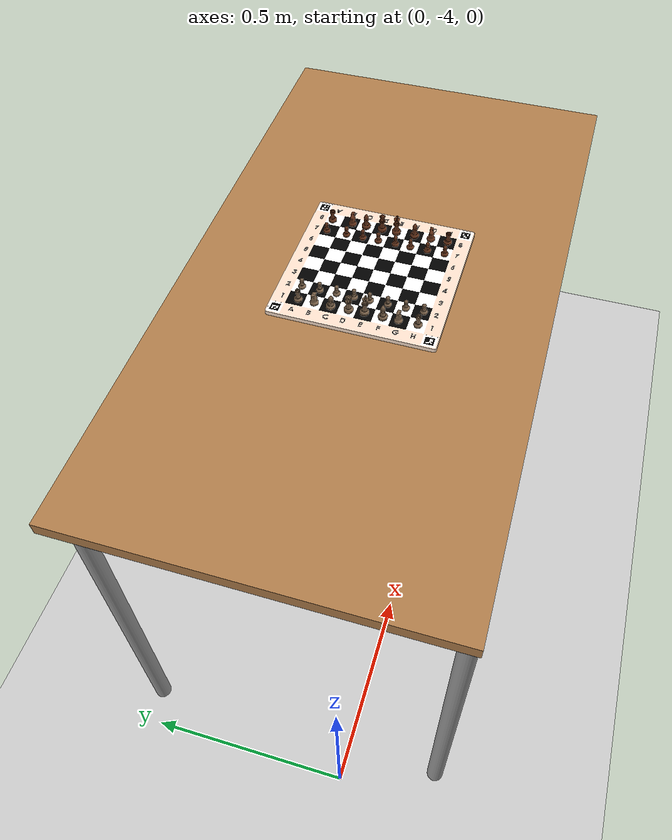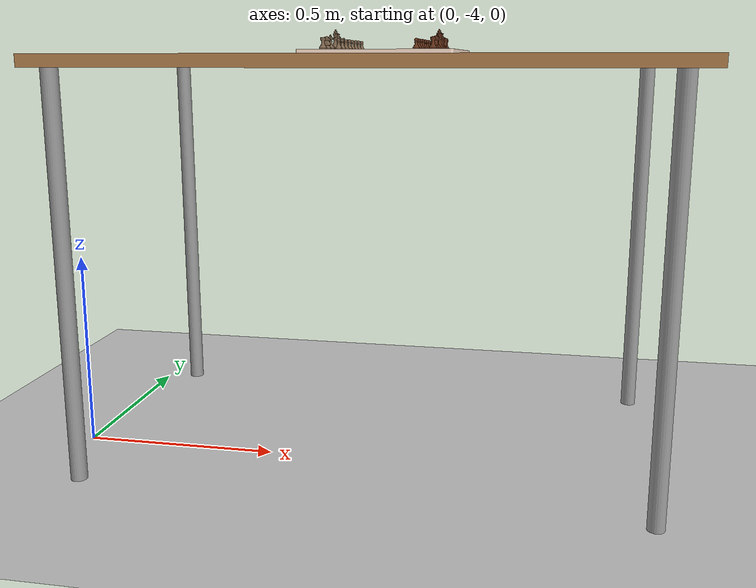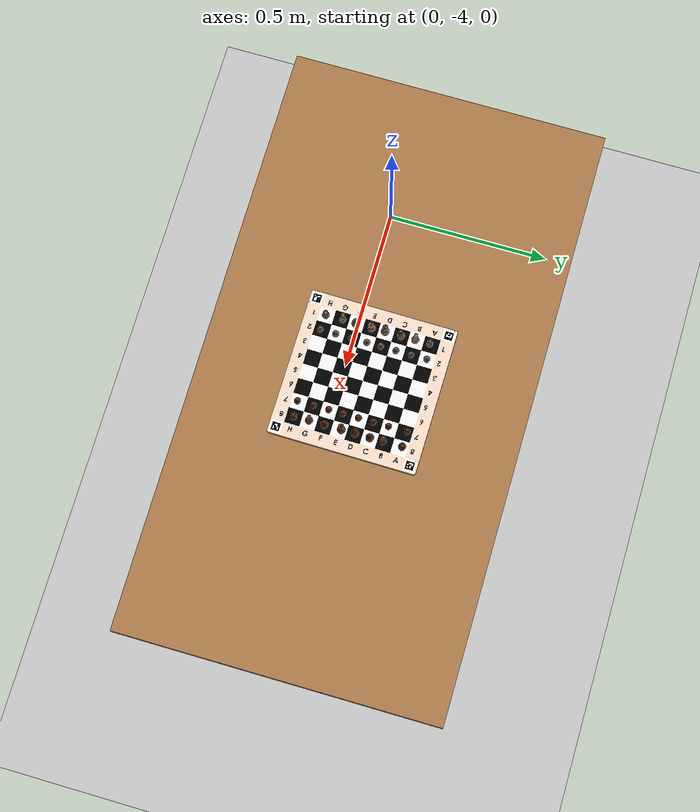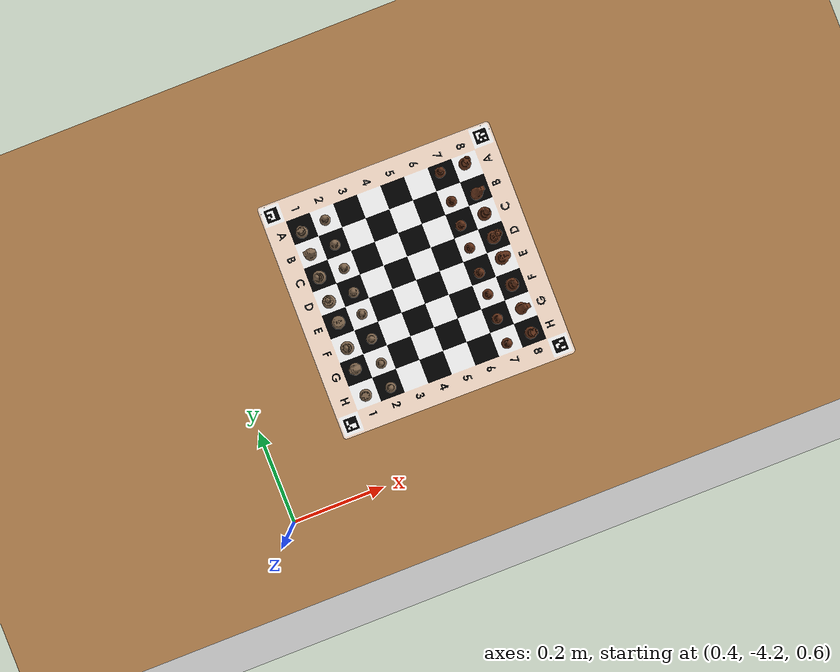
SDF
<sdf version="1.7">
 <world name="default">
  <light name="sun" type="directional">
   <pose>0 0 10 0 -0 0</pose>
   <diffuse>0.8 0.8 0.8 1</diffuse>
   <specular>0.2 0.2 0.2 1</specular>
   <attenuation>
    <range>1000</range>
    <constant>0.9</constant>
    <linear>0.01</linear>
    <quadratic>0.001</quadratic>
   </attenuation>
   <direction>-0.5 0.1 -0.9</direction>
   <spot><inner_angle>0</inner_angle><outer_angle>0</outer_angle><falloff>0</falloff></spot>
  </light>
  <model name="ground_plane">
   <static>1</static>
   <link name="link">
    <collision name="collision">
     <geometry><plane><normal>0 0 1</normal><size>100 100</size></plane></geometry>
     <surface>
      <contact><collide_bitmask>65535</collide_bitmask></contact>
      <friction><ode><mu>100</mu><mu2>50</mu2></ode></friction>
     </surface>
    </collision>
    <visual name="visual">
     <cast_shadows>0</cast_shadows>
     <geometry><plane><normal>0 0 1</normal><size>100 100</size></plane></geometry>
     <material>
      <script><uri>file://media/materials/scripts/gazebo.material</uri><name>Gazebo/Grey</name></script>
     </material>
    </visual>
   </link>
  </model>
  <gravity>0 0 -9.8</gravity>
  <magnetic_field>6e-06 2.3e-05 -4.2e-05</magnetic_field>
  <atmosphere type="adiabatic"/>
  <physics type="ode">
   <max_step_size>0.001</max_step_size>
   <real_time_factor>1</real_time_factor>
   <real_time_update_rate>1000</real_time_update_rate>
  </physics>
  <scene><ambient>0.4 0.4 0.4 1</ambient><background>0.7 0.7 0.7 1</background><shadows>1</shadows></scene>
  <spherical_coordinates>
   <surface_model>EARTH_WGS84</surface_model>
   <latitude_deg>0</latitude_deg>
   <longitude_deg>0</longitude_deg>
   <elevation>0</elevation>
   <heading_deg>0</heading_deg>
  </spherical_coordinates>
  <model name="chessboard">
   <static>1</static>
   <link name="link_0">
    <inertial>
     <mass>1</mass>
     <inertia>
      <ixx>0.166667</ixx>
      <ixy>0</ixy>
      <ixz>0</ixz>
      <iyy>0.166667</iyy>
      <iyz>0</iyz>
      <izz>0.166667</izz>
     </inertia>
    </inertial>
    <visual name="visual">
     <geometry><mesh><uri>model://chessboard/meshes/chessboard.dae</uri><scale>1 1 1</scale></mesh></geometry>
    </visual>
    <collision name="collision">
     <pose>0 0 0.005 0 -0 0</pose>
     <geometry><box><size>0.368 0.368 0.01</size></box></geometry>
     <surface>
      <friction><ode><mu>1</mu><mu2>1</mu2></ode></friction>
      <contact><ode><kp>1e+07</kp><kd>1</kd><max_vel>0.001</max_vel><min_depth>0.1</min_depth></ode></contact>
     </surface>
    </collision>
   </link>
   <pose>0.781691 -3.85293 1.01612 0 -0 3.13138</pose>
  </model>
  <model name="king_white">
   <static>0</static>
   <link name="link_0">
    <inertial>
     <mass>0.1</mass>
     <inertia><ixx>1e-06</ixx><ixy>0</ixy><ixz>0</ixz><iyy>1e-06</iyy><iyz>0</iyz><izz>5e-07</izz></inertia>
    </inertial>
    <visual name="visual">
     <geometry><mesh><uri>model://king_white/meshes/king.dae</uri><scale>1 1 1</scale></mesh></geometry>
     <material>
      <lighting>1</lighting>
      <script><uri>file://media/materials/scripts/gazebo.material</uri><name>Gazebo/Grey</name></script>
      <shader type="vertex"><normal_map>__default__</normal_map></shader>
      <ambient>1 0.894 0.71 1</ambient>
      <diffuse>0.5 0.4 0.3 1</diffuse>
      <specular>0.01 0.01 0.01 1</specular>
      <emissive>0 0 0 1</emissive>
     </material>
    </visual>
    <collision name="collision">
     <pose>0 0 0.005 0 -0 0</pose>
     <geometry><box><size>0.02 0.02 0.01</size></box></geometry>
     <surface>
      <friction>
       <ode><mu>1</mu><mu2>1</mu2><fdir1>0 0 0</fdir1><slip1>0</slip1><slip2>0</slip2></ode>
       <torsional>
        <coefficient>1</coefficient>
        <patch_radius>0</patch_radius>
        <surface_radius>0</surface_radius>
        <use_patch_radius>1</use_patch_radius>
        <ode><slip>0</slip></ode>
       </torsional>
      </friction>
      <bounce><restitution_coefficient>0</restitution_coefficient><threshold>1e+06</threshold></bounce>
      <contact>
       <collide_without_contact>0</collide_without_contact>
       <collide_without_contact_bitmask>1</collide_without_contact_bitmask>
       <collide_bitmask>1</collide_bitmask>
       <ode>
        <soft_cfm>0.1</soft_cfm>
        <soft_erp>0.2</soft_erp>
        <kp>1e+13</kp>
        <kd>1</kd>
        <max_vel>0.01</max_vel>
        <min_depth>0</min_depth>
       </ode>
      </contact>
     </surface>
    </collision>
   </link>
   <static>0</static>
   <pose>0.650924 -3.86927 1.02638 0.031884 0.061759 -0.010427</pose>
  </model>
  <model name="queen_white">
   <static>0</static>
   <link name="link_0">
    <inertial>
     <mass>0.01</mass>
     <inertia><ixx>1e-06</ixx><ixy>0</ixy><ixz>0</ixz><iyy>1e-06</iyy><iyz>0</iyz><izz>5e-07</izz></inertia>
    </inertial>
    <visual name="visual">
     <geometry><mesh><uri>model://queen_white/meshes/queen.dae</uri><scale>1 1 1</scale></mesh></geometry>
     <material>
      <lighting>1</lighting>
      <script><uri>file://media/materials/scripts/gazebo.material</uri><name>Gazebo/Grey</name></script>
      <shader type="vertex"><normal_map>__default__</normal_map></shader>
      <ambient>1 0.894 0.71 1</ambient>
      <diffuse>0.5 0.4 0.3 1</diffuse>
      <specular>0.01 0.01 0.01 1</specular>
      <emissive>0 0 0 1</emissive>
     </material>
    </visual>
    <collision name="collision">
     <pose>0 0 0.005 0 -0 0</pose>
     <geometry><box><size>0.02 0.02 0.01</size></box></geometry>
     <surface>
      <friction>
       <ode><mu>1</mu><mu2>1</mu2><fdir1>0 0 0</fdir1><slip1>0</slip1><slip2>0</slip2></ode>
       <torsional>
        <coefficient>1</coefficient>
        <patch_radius>0</patch_radius>
        <surface_radius>0</surface_radius>
        <use_patch_radius>1</use_patch_radius>
        <ode><slip>0</slip></ode>
       </torsional>
      </friction>
      <bounce><restitution_coefficient>0</restitution_coefficient><threshold>1e+06</threshold></bounce>
      <contact>
       <collide_without_contact>0</collide_without_contact>
       <collide_without_contact_bitmask>1</collide_without_contact_bitmask>
       <collide_bitmask>1</collide_bitmask>
       <ode>
        <soft_cfm>0</soft_cfm>
        <soft_erp>0.2</soft_erp>
        <kp>1e+13</kp>
        <kd>1</kd>
        <max_vel>0.01</max_vel>
        <min_depth>0</min_depth>
       </ode>
       <bullet>
        <split_impulse>1</split_impulse>
        <split_impulse_penetration_threshold>-0.01</split_impulse_penetration_threshold>
        <soft_cfm>0</soft_cfm>
        <soft_erp>0.2</soft_erp>
        <kp>1e+13</kp>
        <kd>1</kd>
       </bullet>
      </contact>
     </surface>
    </collision>
   </link>
   <static>0</static>
   <pose>0.64959 -3.83568 1.02612 0 0 0</pose>
  </model>
  <model name="bishop_white">
   <static>0</static>
   <link name="link_0">
    <inertial>
     <mass>0.01</mass>
     <inertia><ixx>1e-06</ixx><ixy>0</ixy><ixz>0</ixz><iyy>1e-06</iyy><iyz>0</iyz><izz>5e-07</izz></inertia>
    </inertial>
    <visual name="visual">
     <geometry><mesh><uri>model://bishop_white/meshes/bishop.dae</uri><scale>1 1 1</scale></mesh></geometry>
     <material>
      <lighting>1</lighting>
      <script><uri>file://media/materials/scripts/gazebo.material</uri><name>Gazebo/Grey</name></script>
      <shader type="vertex"><normal_map>__default__</normal_map></shader>
      <ambient>1 0.894 0.71 1</ambient>
      <diffuse>0.5 0.4 0.3 1</diffuse>
      <specular>0.01 0.01 0.01 1</specular>
      <emissive>0 0 0 1</emissive>
     </material>
    </visual>
    <collision name="collision">
     <pose>0 0 0.005 0 -0 0</pose>
     <geometry><box><size>0.02 0.02 0.01</size></box></geometry>
     <surface>
      <friction>
       <ode><mu>1</mu><mu2>1</mu2><fdir1>0 0 0</fdir1><slip1>0</slip1><slip2>0</slip2></ode>
       <torsional>
        <coefficient>1</coefficient>
        <patch_radius>0</patch_radius>
        <surface_radius>0</surface_radius>
        <use_patch_radius>1</use_patch_radius>
        <ode><slip>0</slip></ode>
       </torsional>
      </friction>
      <bounce><restitution_coefficient>0</restitution_coefficient><threshold>1e+06</threshold></bounce>
      <contact>
       <collide_without_contact>0</collide_without_contact>
       <collide_without_contact_bitmask>1</collide_without_contact_bitmask>
       <collide_bitmask>1</collide_bitmask>
       <ode>
        <soft_cfm>0</soft_cfm>
        <soft_erp>0.2</soft_erp>
        <kp>1e+13</kp>
        <kd>1</kd>
        <max_vel>0.01</max_vel>
        <min_depth>0</min_depth>
       </ode>
       <bullet>
        <split_impulse>1</split_impulse>
        <split_impulse_penetration_threshold>-0.01</split_impulse_penetration_threshold>
        <soft_cfm>0</soft_cfm>
        <soft_erp>0.2</soft_erp>
        <kp>1e+13</kp>
        <kd>1</kd>
       </bullet>
      </contact>
     </surface>
    </collision>
   </link>
   <static>0</static>
   <pose>0.649592 -3.79638 1.02517 0.073436 -0.073134 -0.004369</pose>
  </model>
  <model name="bishop_white_clone_0">
   <static>0</static>
   <link name="link_0">
    <inertial>
     <mass>0.01</mass>
     <inertia><ixx>1e-06</ixx><ixy>0</ixy><ixz>0</ixz><iyy>1e-06</iyy><iyz>0</iyz><izz>5e-07</izz></inertia>
    </inertial>
    <visual name="visual">
     <geometry><mesh><uri>model://bishop_white/meshes/bishop.dae</uri><scale>1 1 1</scale></mesh></geometry>
     <material>
      <lighting>1</lighting>
      <script><uri>file://media/materials/scripts/gazebo.material</uri><name>Gazebo/Grey</name></script>
      <shader type="vertex"><normal_map>__default__</normal_map></shader>
      <ambient>1 0.894 0.71 1</ambient>
      <diffuse>0.5 0.4 0.3 1</diffuse>
      <specular>0.01 0.01 0.01 1</specular>
      <emissive>0 0 0 1</emissive>
     </material>
    </visual>
    <collision name="collision">
     <pose>0 0 0.005 0 -0 0</pose>
     <geometry><box><size>0.02 0.02 0.01</size></box></geometry>
     <surface>
      <friction>
       <ode><mu>1</mu><mu2>1</mu2><fdir1>0 0 0</fdir1><slip1>0</slip1><slip2>0</slip2></ode>
       <torsional>
        <coefficient>1</coefficient>
        <patch_radius>0</patch_radius>
        <surface_radius>0</surface_radius>
        <use_patch_radius>1</use_patch_radius>
        <ode><slip>0</slip></ode>
       </torsional>
      </friction>
      <bounce><restitution_coefficient>0</restitution_coefficient><threshold>1e+06</threshold></bounce>
      <contact>
       <collide_without_contact>0</collide_without_contact>
       <collide_without_contact_bitmask>1</collide_without_contact_bitmask>
       <collide_bitmask>1</collide_bitmask>
       <ode>
        <soft_cfm>0</soft_cfm>
        <soft_erp>0.2</soft_erp>
        <kp>1e+13</kp>
        <kd>1</kd>
        <max_vel>0.01</max_vel>
        <min_depth>0</min_depth>
       </ode>
       <bullet>
        <split_impulse>1</split_impulse>
        <split_impulse_penetration_threshold>-0.01</split_impulse_penetration_threshold>
        <soft_cfm>0</soft_cfm>
        <soft_erp>0.2</soft_erp>
        <kp>1e+13</kp>
        <kd>1</kd>
       </bullet>
      </contact>
     </surface>
    </collision>
   </link>
   <static>0</static>
   <pose>0.64959 -3.90934 1.02612 0 0 0</pose>
  </model>
  <model name="knight_white">
   <static>0</static>
   <link name="link_0">
    <inertial>
     <mass>0.01</mass>
     <inertia><ixx>1e-06</ixx><ixy>0</ixy><ixz>0</ixz><iyy>1e-06</iyy><iyz>0</iyz><izz>5e-07</izz></inertia>
    </inertial>
    <visual name="visual">
     <geometry><mesh><uri>model://knight_white/meshes/knight.dae</uri><scale>1 1 1</scale></mesh></geometry>
     <material>
      <lighting>1</lighting>
      <script><uri>file://media/materials/scripts/gazebo.material</uri><name>Gazebo/Grey</name></script>
      <shader type="vertex"><normal_map>__default__</normal_map></shader>
      <ambient>1 0.894 0.71 1</ambient>
      <diffuse>0.5 0.4 0.3 1</diffuse>
      <specular>0.01 0.01 0.01 1</specular>
      <emissive>0 0 0 1</emissive>
     </material>
    </visual>
    <collision name="collision">
     <pose>0 0 0.005 0 -0 0</pose>
     <geometry><box><size>0.018 0.018 0.01</size></box></geometry>
     <surface>
      <friction>
       <ode><mu>1</mu><mu2>1</mu2><fdir1>0 0 0</fdir1><slip1>0</slip1><slip2>0</slip2></ode>
       <torsional>
        <coefficient>1</coefficient>
        <patch_radius>0</patch_radius>
        <surface_radius>0</surface_radius>
        <use_patch_radius>1</use_patch_radius>
        <ode><slip>0</slip></ode>
       </torsional>
      </friction>
      <bounce><restitution_coefficient>0</restitution_coefficient><threshold>1e+06</threshold></bounce>
      <contact>
       <collide_without_contact>0</collide_without_contact>
       <collide_without_contact_bitmask>1</collide_without_contact_bitmask>
       <collide_bitmask>1</collide_bitmask>
       <ode>
        <soft_cfm>0</soft_cfm>
        <soft_erp>0.2</soft_erp>
        <kp>1e+13</kp>
        <kd>1</kd>
        <max_vel>0.01</max_vel>
        <min_depth>0</min_depth>
       </ode>
       <bullet>
        <split_impulse>1</split_impulse>
        <split_impulse_penetration_threshold>-0.01</split_impulse_penetration_threshold>
        <soft_cfm>0</soft_cfm>
        <soft_erp>0.2</soft_erp>
        <kp>1e+13</kp>
        <kd>1</kd>
       </bullet>
      </contact>
     </surface>
    </collision>
   </link>
   <static>0</static>
   <pose>0.64969 -3.94259 1.02612 0 0 1.57236</pose>
  </model>
  <model name="knight_white_clone">
   <static>0</static>
   <link name="link_0">
    <inertial>
     <mass>0.01</mass>
     <inertia><ixx>1e-06</ixx><ixy>0</ixy><ixz>0</ixz><iyy>1e-06</iyy><iyz>0</iyz><izz>5e-07</izz></inertia>
    </inertial>
    <visual name="visual">
     <geometry><mesh><uri>model://knight_white/meshes/knight.dae</uri><scale>1 1 1</scale></mesh></geometry>
     <material>
      <lighting>1</lighting>
      <script><uri>file://media/materials/scripts/gazebo.material</uri><name>Gazebo/Grey</name></script>
      <shader type="vertex"><normal_map>__default__</normal_map></shader>
      <ambient>1 0.894 0.71 1</ambient>
      <diffuse>0.5 0.4 0.3 1</diffuse>
      <specular>0.01 0.01 0.01 1</specular>
      <emissive>0 0 0 1</emissive>
     </material>
    </visual>
    <collision name="collision">
     <pose>0 0 0.005 0 -0 0</pose>
     <geometry><box><size>0.018 0.018 0.01</size></box></geometry>
     <surface>
      <friction>
       <ode><mu>1</mu><mu2>1</mu2><fdir1>0 0 0</fdir1><slip1>0</slip1><slip2>0</slip2></ode>
       <torsional>
        <coefficient>1</coefficient>
        <patch_radius>0</patch_radius>
        <surface_radius>0</surface_radius>
        <use_patch_radius>1</use_patch_radius>
        <ode><slip>0</slip></ode>
       </torsional>
      </friction>
      <bounce><restitution_coefficient>0</restitution_coefficient><threshold>1e+06</threshold></bounce>
      <contact>
       <collide_without_contact>0</collide_without_contact>
       <collide_without_contact_bitmask>1</collide_without_contact_bitmask>
       <collide_bitmask>1</collide_bitmask>
       <ode>
        <soft_cfm>0</soft_cfm>
        <soft_erp>0.2</soft_erp>
        <kp>1e+13</kp>
        <kd>1</kd>
        <max_vel>0.01</max_vel>
        <min_depth>0</min_depth>
       </ode>
       <bullet>
        <split_impulse>1</split_impulse>
        <split_impulse_penetration_threshold>-0.01</split_impulse_penetration_threshold>
        <soft_cfm>0</soft_cfm>
        <soft_erp>0.2</soft_erp>
        <kp>1e+13</kp>
        <kd>1</kd>
       </bullet>
      </contact>
     </surface>
    </collision>
   </link>
   <static>0</static>
   <pose>0.649681 -3.76045 1.02612 0 0 1.57236</pose>
  </model>
  <model name="rook_white">
   <static>0</static>
   <link name="link_0">
    <inertial>
     <mass>0.01</mass>
     <inertia><ixx>1e-06</ixx><ixy>0</ixy><ixz>0</ixz><iyy>1e-06</iyy><iyz>0</iyz><izz>5e-07</izz></inertia>
    </inertial>
    <visual name="visual">
     <geometry><mesh><uri>model://rook_white/meshes/rook.dae</uri><scale>1 1 1</scale></mesh></geometry>
     <material>
      <lighting>1</lighting>
      <script><uri>file://media/materials/scripts/gazebo.material</uri><name>Gazebo/Grey</name></script>
      <shader type="vertex"><normal_map>__default__</normal_map></shader>
      <ambient>1 0.894 0.71 1</ambient>
      <diffuse>0.5 0.4 0.3 1</diffuse>
      <specular>0.01 0.01 0.01 1</specular>
      <emissive>0 0 0 1</emissive>
     </material>
    </visual>
    <collision name="collision">
     <pose>0 0 0.005 0 -0 0</pose>
     <geometry><box><size>0.018 0.018 0.01</size></box></geometry>
     <surface>
      <friction>
       <ode><mu>1</mu><mu2>1</mu2><fdir1>0 0 0</fdir1><slip1>0</slip1><slip2>0</slip2></ode>
       <torsional>
        <coefficient>1</coefficient>
        <patch_radius>0</patch_radius>
        <surface_radius>0</surface_radius>
        <use_patch_radius>1</use_patch_radius>
        <ode><slip>0</slip></ode>
       </torsional>
      </friction>
      <bounce><restitution_coefficient>0</restitution_coefficient><threshold>1e+06</threshold></bounce>
      <contact>
       <collide_without_contact>0</collide_without_contact>
       <collide_without_contact_bitmask>1</collide_without_contact_bitmask>
       <collide_bitmask>1</collide_bitmask>
       <ode>
        <soft_cfm>0</soft_cfm>
        <soft_erp>0.2</soft_erp>
        <kp>1e+13</kp>
        <kd>1</kd>
        <max_vel>0.01</max_vel>
        <min_depth>0</min_depth>
       </ode>
       <bullet>
        <split_impulse>1</split_impulse>
        <split_impulse_penetration_threshold>-0.01</split_impulse_penetration_threshold>
        <soft_cfm>0</soft_cfm>
        <soft_erp>0.2</soft_erp>
        <kp>1e+13</kp>
        <kd>1</kd>
       </bullet>
      </contact>
     </surface>
    </collision>
   </link>
   <static>0</static>
   <pose>0.64949 -3.72491 1.02612 0 0 -0</pose>
  </model>
  <model name="rook_white_clone">
   <static>0</static>
   <link name="link_0">
    <inertial>
     <mass>0.01</mass>
     <inertia><ixx>1e-06</ixx><ixy>0</ixy><ixz>0</ixz><iyy>1e-06</iyy><iyz>0</iyz><izz>5e-07</izz></inertia>
    </inertial>
    <visual name="visual">
     <geometry><mesh><uri>model://rook_white/meshes/rook.dae</uri><scale>1 1 1</scale></mesh></geometry>
     <material>
      <lighting>1</lighting>
      <script><uri>file://media/materials/scripts/gazebo.material</uri><name>Gazebo/Grey</name></script>
      <shader type="vertex"><normal_map>__default__</normal_map></shader>
      <ambient>1 0.894 0.71 1</ambient>
      <diffuse>0.5 0.4 0.3 1</diffuse>
      <specular>0.01 0.01 0.01 1</specular>
      <emissive>0 0 0 1</emissive>
     </material>
    </visual>
    <collision name="collision">
     <pose>0 0 0.005 0 -0 0</pose>
     <geometry><box><size>0.018 0.018 0.01</size></box></geometry>
     <surface>
      <friction>
       <ode><mu>1</mu><mu2>1</mu2><fdir1>0 0 0</fdir1><slip1>0</slip1><slip2>0</slip2></ode>
       <torsional>
        <coefficient>1</coefficient>
        <patch_radius>0</patch_radius>
        <surface_radius>0</surface_radius>
        <use_patch_radius>1</use_patch_radius>
        <ode><slip>0</slip></ode>
       </torsional>
      </friction>
      <bounce><restitution_coefficient>0</restitution_coefficient><threshold>1e+06</threshold></bounce>
      <contact>
       <collide_without_contact>0</collide_without_contact>
       <collide_without_contact_bitmask>1</collide_without_contact_bitmask>
       <collide_bitmask>1</collide_bitmask>
       <ode>
        <soft_cfm>0</soft_cfm>
        <soft_erp>0.2</soft_erp>
        <kp>1e+13</kp>
        <kd>1</kd>
        <max_vel>0.01</max_vel>
        <min_depth>0</min_depth>
       </ode>
       <bullet>
        <split_impulse>1</split_impulse>
        <split_impulse_penetration_threshold>-0.01</split_impulse_penetration_threshold>
        <soft_cfm>0</soft_cfm>
        <soft_erp>0.2</soft_erp>
        <kp>1e+13</kp>
        <kd>1</kd>
       </bullet>
      </contact>
     </surface>
    </collision>
   </link>
   <static>0</static>
   <pose>0.64949 -3.98428 1.02612 0 0 0</pose>
  </model>
  <model name="pawn_white">
   <static>0</static>
   <link name="link_0">
    <inertial>
     <mass>0.01</mass>
     <inertia><ixx>1e-06</ixx><ixy>0</ixy><ixz>0</ixz><iyy>1e-06</iyy><iyz>0</iyz><izz>5e-07</izz></inertia>
    </inertial>
    <visual name="visual">
     <geometry><mesh><uri>model://pawn_white/meshes/pawn.dae</uri><scale>1 1 1</scale></mesh></geometry>
     <material>
      <lighting>1</lighting>
      <script><uri>file://media/materials/scripts/gazebo.material</uri><name>Gazebo/Grey</name></script>
      <shader type="vertex"><normal_map>__default__</normal_map></shader>
      <ambient>1 0.894 0.71 1</ambient>
      <diffuse>0.5 0.4 0.3 1</diffuse>
      <specular>0.01 0.01 0.01 1</specular>
      <emissive>0 0 0 1</emissive>
     </material>
    </visual>
    <collision name="collision">
     <pose>0 0 0.005 0 -0 0</pose>
     <geometry><box><size>0.016 0.016 0.01</size></box></geometry>
     <surface>
      <friction>
       <ode><mu>1</mu><mu2>1</mu2><fdir1>0 0 0</fdir1><slip1>0</slip1><slip2>0</slip2></ode>
       <torsional>
        <coefficient>1</coefficient>
        <patch_radius>0</patch_radius>
        <surface_radius>0</surface_radius>
        <use_patch_radius>1</use_patch_radius>
        <ode><slip>0</slip></ode>
       </torsional>
      </friction>
      <bounce><restitution_coefficient>0</restitution_coefficient><threshold>1e+06</threshold></bounce>
      <contact>
       <collide_without_contact>0</collide_without_contact>
       <collide_without_contact_bitmask>1</collide_without_contact_bitmask>
       <collide_bitmask>1</collide_bitmask>
       <ode>
        <soft_cfm>0</soft_cfm>
        <soft_erp>0.2</soft_erp>
        <kp>1e+13</kp>
        <kd>1</kd>
        <max_vel>0.01</max_vel>
        <min_depth>0</min_depth>
       </ode>
       <bullet>
        <split_impulse>1</split_impulse>
        <split_impulse_penetration_threshold>-0.01</split_impulse_penetration_threshold>
        <soft_cfm>0</soft_cfm>
        <soft_erp>0.2</soft_erp>
        <kp>1e+13</kp>
        <kd>1</kd>
       </bullet>
      </contact>
     </surface>
    </collision>
   </link>
   <static>0</static>
   <pose>0.688245 -3.83616 1.02612 0 0 -0</pose>
  </model>
  <model name="pawn_white_clone">
   <static>0</static>
   <link name="link_0">
    <inertial>
     <mass>0.01</mass>
     <inertia><ixx>1e-06</ixx><ixy>0</ixy><ixz>0</ixz><iyy>1e-06</iyy><iyz>0</iyz><izz>5e-07</izz></inertia>
    </inertial>
    <visual name="visual">
     <geometry><mesh><uri>model://pawn_white/meshes/pawn.dae</uri><scale>1 1 1</scale></mesh></geometry>
     <material>
      <lighting>1</lighting>
      <script><uri>file://media/materials/scripts/gazebo.material</uri><name>Gazebo/Grey</name></script>
      <shader type="vertex"><normal_map>__default__</normal_map></shader>
      <ambient>1 0.894 0.71 1</ambient>
      <diffuse>0.5 0.4 0.3 1</diffuse>
      <specular>0.01 0.01 0.01 1</specular>
      <emissive>0 0 0 1</emissive>
     </material>
    </visual>
    <collision name="collision">
     <pose>0 0 0.005 0 -0 0</pose>
     <geometry><box><size>0.016 0.016 0.01</size></box></geometry>
     <surface>
      <friction>
       <ode><mu>1</mu><mu2>1</mu2><fdir1>0 0 0</fdir1><slip1>0</slip1><slip2>0</slip2></ode>
       <torsional>
        <coefficient>1</coefficient>
        <patch_radius>0</patch_radius>
        <surface_radius>0</surface_radius>
        <use_patch_radius>1</use_patch_radius>
        <ode><slip>0</slip></ode>
       </torsional>
      </friction>
      <bounce><restitution_coefficient>0</restitution_coefficient><threshold>1e+06</threshold></bounce>
      <contact>
       <collide_without_contact>0</collide_without_contact>
       <collide_without_contact_bitmask>1</collide_without_contact_bitmask>
       <collide_bitmask>1</collide_bitmask>
       <ode>
        <soft_cfm>0</soft_cfm>
        <soft_erp>0.2</soft_erp>
        <kp>1e+13</kp>
        <kd>1</kd>
        <max_vel>0.01</max_vel>
        <min_depth>0</min_depth>
       </ode>
       <bullet>
        <split_impulse>1</split_impulse>
        <split_impulse_penetration_threshold>-0.01</split_impulse_penetration_threshold>
        <soft_cfm>0</soft_cfm>
        <soft_erp>0.2</soft_erp>
        <kp>1e+13</kp>
        <kd>1</kd>
       </bullet>
      </contact>
     </surface>
    </collision>
   </link>
   <static>0</static>
   <pose>0.688245 -3.79784 1.02612 0 0 -0</pose>
  </model>
  <model name="pawn_white_clone_0">
   <static>0</static>
   <link name="link_0">
    <inertial>
     <mass>0.01</mass>
     <inertia><ixx>1e-06</ixx><ixy>0</ixy><ixz>0</ixz><iyy>1e-06</iyy><iyz>0</iyz><izz>5e-07</izz></inertia>
    </inertial>
    <visual name="visual">
     <geometry><mesh><uri>model://pawn_white/meshes/pawn.dae</uri><scale>1 1 1</scale></mesh></geometry>
     <material>
      <lighting>1</lighting>
      <script><uri>file://media/materials/scripts/gazebo.material</uri><name>Gazebo/Grey</name></script>
      <shader type="vertex"><normal_map>__default__</normal_map></shader>
      <ambient>1 0.894 0.71 1</ambient>
      <diffuse>0.5 0.4 0.3 1</diffuse>
      <specular>0.01 0.01 0.01 1</specular>
      <emissive>0 0 0 1</emissive>
     </material>
    </visual>
    <collision name="collision">
     <pose>0 0 0.005 0 -0 0</pose>
     <geometry><box><size>0.016 0.016 0.01</size></box></geometry>
     <surface>
      <friction>
       <ode><mu>1</mu><mu2>1</mu2><fdir1>0 0 0</fdir1><slip1>0</slip1><slip2>0</slip2></ode>
       <torsional>
        <coefficient>1</coefficient>
        <patch_radius>0</patch_radius>
        <surface_radius>0</surface_radius>
        <use_patch_radius>1</use_patch_radius>
        <ode><slip>0</slip></ode>
       </torsional>
      </friction>
      <bounce><restitution_coefficient>0</restitution_coefficient><threshold>1e+06</threshold></bounce>
      <contact>
       <collide_without_contact>0</collide_without_contact>
       <collide_without_contact_bitmask>1</collide_without_contact_bitmask>
       <collide_bitmask>1</collide_bitmask>
       <ode>
        <soft_cfm>0</soft_cfm>
        <soft_erp>0.2</soft_erp>
        <kp>1e+13</kp>
        <kd>1</kd>
        <max_vel>0.01</max_vel>
        <min_depth>0</min_depth>
       </ode>
       <bullet>
        <split_impulse>1</split_impulse>
        <split_impulse_penetration_threshold>-0.01</split_impulse_penetration_threshold>
        <soft_cfm>0</soft_cfm>
        <soft_erp>0.2</soft_erp>
        <kp>1e+13</kp>
        <kd>1</kd>
       </bullet>
      </contact>
     </surface>
    </collision>
   </link>
   <static>0</static>
   <pose>0.688245 -3.98716 1.02612 0 0 0</pose>
  </model>
  <model name="pawn_white_clone_1">
   <static>0</static>
   <link name="link_0">
    <inertial>
     <mass>0.01</mass>
     <inertia><ixx>1e-06</ixx><ixy>0</ixy><ixz>0</ixz><iyy>1e-06</iyy><iyz>0</iyz><izz>5e-07</izz></inertia>
    </inertial>
    <visual name="visual">
     <geometry><mesh><uri>model://pawn_white/meshes/pawn.dae</uri><scale>1 1 1</scale></mesh></geometry>
     <material>
      <lighting>1</lighting>
      <script><uri>file://media/materials/scripts/gazebo.material</uri><name>Gazebo/Grey</name></script>
      <shader type="vertex"><normal_map>__default__</normal_map></shader>
      <ambient>1 0.894 0.71 1</ambient>
      <diffuse>0.5 0.4 0.3 1</diffuse>
      <specular>0.01 0.01 0.01 1</specular>
      <emissive>0 0 0 1</emissive>
     </material>
    </visual>
    <collision name="collision">
     <pose>0 0 0.005 0 -0 0</pose>
     <geometry><box><size>0.016 0.016 0.01</size></box></geometry>
     <surface>
      <friction>
       <ode><mu>1</mu><mu2>1</mu2><fdir1>0 0 0</fdir1><slip1>0</slip1><slip2>0</slip2></ode>
       <torsional>
        <coefficient>1</coefficient>
        <patch_radius>0</patch_radius>
        <surface_radius>0</surface_radius>
        <use_patch_radius>1</use_patch_radius>
        <ode><slip>0</slip></ode>
       </torsional>
      </friction>
      <bounce><restitution_coefficient>0</restitution_coefficient><threshold>1e+06</threshold></bounce>
      <contact>
       <collide_without_contact>0</collide_without_contact>
       <collide_without_contact_bitmask>1</collide_without_contact_bitmask>
       <collide_bitmask>1</collide_bitmask>
       <ode>
        <soft_cfm>0</soft_cfm>
        <soft_erp>0.2</soft_erp>
        <kp>1e+13</kp>
        <kd>1</kd>
        <max_vel>0.01</max_vel>
        <min_depth>0</min_depth>
       </ode>
       <bullet>
        <split_impulse>1</split_impulse>
        <split_impulse_penetration_threshold>-0.01</split_impulse_penetration_threshold>
        <soft_cfm>0</soft_cfm>
        <soft_erp>0.2</soft_erp>
        <kp>1e+13</kp>
        <kd>1</kd>
       </bullet>
      </contact>
     </surface>
    </collision>
   </link>
   <static>0</static>
   <pose>0.688245 -3.94848 1.02612 0 0 0</pose>
  </model>
  <model name="pawn_white_clone_2">
   <static>0</static>
   <link name="link_0">
    <inertial>
     <mass>0.01</mass>
     <inertia><ixx>1e-06</ixx><ixy>0</ixy><ixz>0</ixz><iyy>1e-06</iyy><iyz>0</iyz><izz>5e-07</izz></inertia>
    </inertial>
    <visual name="visual">
     <geometry><mesh><uri>model://pawn_white/meshes/pawn.dae</uri><scale>1 1 1</scale></mesh></geometry>
     <material>
      <lighting>1</lighting>
      <script><uri>file://media/materials/scripts/gazebo.material</uri><name>Gazebo/Grey</name></script>
      <shader type="vertex"><normal_map>__default__</normal_map></shader>
      <ambient>1 0.894 0.71 1</ambient>
      <diffuse>0.5 0.4 0.3 1</diffuse>
      <specular>0.01 0.01 0.01 1</specular>
      <emissive>0 0 0 1</emissive>
     </material>
    </visual>
    <collision name="collision">
     <pose>0 0 0.005 0 -0 0</pose>
     <geometry><box><size>0.016 0.016 0.01</size></box></geometry>
     <surface>
      <friction>
       <ode><mu>1</mu><mu2>1</mu2><fdir1>0 0 0</fdir1><slip1>0</slip1><slip2>0</slip2></ode>
       <torsional>
        <coefficient>1</coefficient>
        <patch_radius>0</patch_radius>
        <surface_radius>0</surface_radius>
        <use_patch_radius>1</use_patch_radius>
        <ode><slip>0</slip></ode>
       </torsional>
      </friction>
      <bounce><restitution_coefficient>0</restitution_coefficient><threshold>1e+06</threshold></bounce>
      <contact>
       <collide_without_contact>0</collide_without_contact>
       <collide_without_contact_bitmask>1</collide_without_contact_bitmask>
       <collide_bitmask>1</collide_bitmask>
       <ode>
        <soft_cfm>0</soft_cfm>
        <soft_erp>0.2</soft_erp>
        <kp>1e+13</kp>
        <kd>1</kd>
        <max_vel>0.01</max_vel>
        <min_depth>0</min_depth>
       </ode>
       <bullet>
        <split_impulse>1</split_impulse>
        <split_impulse_penetration_threshold>-0.01</split_impulse_penetration_threshold>
        <soft_cfm>0</soft_cfm>
        <soft_erp>0.2</soft_erp>
        <kp>1e+13</kp>
        <kd>1</kd>
       </bullet>
      </contact>
     </surface>
    </collision>
   </link>
   <static>0</static>
   <pose>0.688245 -3.9097 1.02612 0 0 0</pose>
  </model>
  <model name="pawn_white_clone_3">
   <static>0</static>
   <link name="link_0">
    <inertial>
     <mass>0.01</mass>
     <inertia><ixx>1e-06</ixx><ixy>0</ixy><ixz>0</ixz><iyy>1e-06</iyy><iyz>0</iyz><izz>5e-07</izz></inertia>
    </inertial>
    <visual name="visual">
     <geometry><mesh><uri>model://pawn_white/meshes/pawn.dae</uri><scale>1 1 1</scale></mesh></geometry>
     <material>
      <lighting>1</lighting>
      <script><uri>file://media/materials/scripts/gazebo.material</uri><name>Gazebo/Grey</name></script>
      <shader type="vertex"><normal_map>__default__</normal_map></shader>
      <ambient>1 0.894 0.71 1</ambient>
      <diffuse>0.5 0.4 0.3 1</diffuse>
      <specular>0.01 0.01 0.01 1</specular>
      <emissive>0 0 0 1</emissive>
     </material>
    </visual>
    <collision name="collision">
     <pose>0 0 0.005 0 -0 0</pose>
     <geometry><box><size>0.016 0.016 0.01</size></box></geometry>
     <surface>
      <friction>
       <ode><mu>1</mu><mu2>1</mu2><fdir1>0 0 0</fdir1><slip1>0</slip1><slip2>0</slip2></ode>
       <torsional>
        <coefficient>1</coefficient>
        <patch_radius>0</patch_radius>
        <surface_radius>0</surface_radius>
        <use_patch_radius>1</use_patch_radius>
        <ode><slip>0</slip></ode>
       </torsional>
      </friction>
      <bounce><restitution_coefficient>0</restitution_coefficient><threshold>1e+06</threshold></bounce>
      <contact>
       <collide_without_contact>0</collide_without_contact>
       <collide_without_contact_bitmask>1</collide_without_contact_bitmask>
       <collide_bitmask>1</collide_bitmask>
       <ode>
        <soft_cfm>0</soft_cfm>
        <soft_erp>0.2</soft_erp>
        <kp>1e+13</kp>
        <kd>1</kd>
        <max_vel>0.01</max_vel>
        <min_depth>0</min_depth>
       </ode>
       <bullet>
        <split_impulse>1</split_impulse>
        <split_impulse_penetration_threshold>-0.01</split_impulse_penetration_threshold>
        <soft_cfm>0</soft_cfm>
        <soft_erp>0.2</soft_erp>
        <kp>1e+13</kp>
        <kd>1</kd>
       </bullet>
      </contact>
     </surface>
    </collision>
   </link>
   <static>0</static>
   <pose>0.688245 -3.8705 1.02612 0 0 -0</pose>
  </model>
  <model name="pawn_white_clone_4">
   <static>0</static>
   <link name="link_0">
    <inertial>
     <mass>0.01</mass>
     <inertia><ixx>1e-06</ixx><ixy>0</ixy><ixz>0</ixz><iyy>1e-06</iyy><iyz>0</iyz><izz>5e-07</izz></inertia>
    </inertial>
    <visual name="visual">
     <geometry><mesh><uri>model://pawn_white/meshes/pawn.dae</uri><scale>1 1 1</scale></mesh></geometry>
     <material>
      <lighting>1</lighting>
      <script><uri>file://media/materials/scripts/gazebo.material</uri><name>Gazebo/Grey</name></script>
      <shader type="vertex"><normal_map>__default__</normal_map></shader>
      <ambient>1 0.894 0.71 1</ambient>
      <diffuse>0.5 0.4 0.3 1</diffuse>
      <specular>0.01 0.01 0.01 1</specular>
      <emissive>0 0 0 1</emissive>
     </material>
    </visual>
    <collision name="collision">
     <pose>0 0 0.005 0 -0 0</pose>
     <geometry><box><size>0.016 0.016 0.01</size></box></geometry>
     <surface>
      <friction>
       <ode><mu>1</mu><mu2>1</mu2><fdir1>0 0 0</fdir1><slip1>0</slip1><slip2>0</slip2></ode>
       <torsional>
        <coefficient>1</coefficient>
        <patch_radius>0</patch_radius>
        <surface_radius>0</surface_radius>
        <use_patch_radius>1</use_patch_radius>
        <ode><slip>0</slip></ode>
       </torsional>
      </friction>
      <bounce><restitution_coefficient>0</restitution_coefficient><threshold>1e+06</threshold></bounce>
      <contact>
       <collide_without_contact>0</collide_without_contact>
       <collide_without_contact_bitmask>1</collide_without_contact_bitmask>
       <collide_bitmask>1</collide_bitmask>
       <ode>
        <soft_cfm>0</soft_cfm>
        <soft_erp>0.2</soft_erp>
        <kp>1e+13</kp>
        <kd>1</kd>
        <max_vel>0.01</max_vel>
        <min_depth>0</min_depth>
       </ode>
       <bullet>
        <split_impulse>1</split_impulse>
        <split_impulse_penetration_threshold>-0.01</split_impulse_penetration_threshold>
        <soft_cfm>0</soft_cfm>
        <soft_erp>0.2</soft_erp>
        <kp>1e+13</kp>
        <kd>1</kd>
       </bullet>
      </contact>
     </surface>
    </collision>
   </link>
   <static>0</static>
   <pose>0.688245 -3.76037 1.02612 0 0 -0</pose>
  </model>
  <model name="pawn_white_clone_5">
   <static>0</static>
   <link name="link_0">
    <inertial>
     <mass>0.01</mass>
     <inertia><ixx>1e-06</ixx><ixy>0</ixy><ixz>0</ixz><iyy>1e-06</iyy><iyz>0</iyz><izz>5e-07</izz></inertia>
    </inertial>
    <visual name="visual">
     <geometry><mesh><uri>model://pawn_white/meshes/pawn.dae</uri><scale>1 1 1</scale></mesh></geometry>
     <material>
      <lighting>1</lighting>
      <script><uri>file://media/materials/scripts/gazebo.material</uri><name>Gazebo/Grey</name></script>
      <shader type="vertex"><normal_map>__default__</normal_map></shader>
      <ambient>1 0.894 0.71 1</ambient>
      <diffuse>0.5 0.4 0.3 1</diffuse>
      <specular>0.01 0.01 0.01 1</specular>
      <emissive>0 0 0 1</emissive>
     </material>
    </visual>
    <collision name="collision">
     <pose>0 0 0.005 0 -0 0</pose>
     <geometry><box><size>0.016 0.016 0.01</size></box></geometry>
     <surface>
      <friction>
       <ode><mu>1</mu><mu2>1</mu2><fdir1>0 0 0</fdir1><slip1>0</slip1><slip2>0</slip2></ode>
       <torsional>
        <coefficient>1</coefficient>
        <patch_radius>0</patch_radius>
        <surface_radius>0</surface_radius>
        <use_patch_radius>1</use_patch_radius>
        <ode><slip>0</slip></ode>
       </torsional>
      </friction>
      <bounce><restitution_coefficient>0</restitution_coefficient><threshold>1e+06</threshold></bounce>
      <contact>
       <collide_without_contact>0</collide_without_contact>
       <collide_without_contact_bitmask>1</collide_without_contact_bitmask>
       <collide_bitmask>1</collide_bitmask>
       <ode>
        <soft_cfm>0</soft_cfm>
        <soft_erp>0.2</soft_erp>
        <kp>1e+13</kp>
        <kd>1</kd>
        <max_vel>0.01</max_vel>
        <min_depth>0</min_depth>
       </ode>
       <bullet>
        <split_impulse>1</split_impulse>
        <split_impulse_penetration_threshold>-0.01</split_impulse_penetration_threshold>
        <soft_cfm>0</soft_cfm>
        <soft_erp>0.2</soft_erp>
        <kp>1e+13</kp>
        <kd>1</kd>
       </bullet>
      </contact>
     </surface>
    </collision>
   </link>
   <static>0</static>
   <pose>0.688245 -3.72086 1.02612 0 0 -0</pose>
  </model>
  <model name="king_black">
   <static>0</static>
   <link name="link_0">
    <inertial>
     <mass>0.1</mass>
     <inertia><ixx>1e-06</ixx><ixy>0</ixy><ixz>0</ixz><iyy>1e-06</iyy><iyz>0</iyz><izz>5e-07</izz></inertia>
    </inertial>
    <visual name="visual">
     <geometry><mesh><uri>model://king_black/meshes/king.dae</uri><scale>1 1 1</scale></mesh></geometry>
     <material>
      <lighting>1</lighting>
      <script><uri>file://media/materials/scripts/gazebo.material</uri><name>Gazebo/Grey</name></script>
      <shader type="vertex"><normal_map>__default__</normal_map></shader>
      <ambient>0.62 0.31 0.12 1</ambient>
      <diffuse>0.4 0.2 0.1 1</diffuse>
      <specular>0.01 0.01 0.01 1</specular>
      <emissive>0 0 0 1</emissive>
     </material>
    </visual>
    <collision name="collision">
     <pose>0 0 0.005 0 -0 0</pose>
     <geometry><box><size>0.02 0.02 0.01</size></box></geometry>
     <surface>
      <friction>
       <ode><mu>1</mu><mu2>1</mu2><fdir1>0 0 0</fdir1><slip1>0</slip1><slip2>0</slip2></ode>
       <torsional>
        <coefficient>1</coefficient>
        <patch_radius>0</patch_radius>
        <surface_radius>0</surface_radius>
        <use_patch_radius>1</use_patch_radius>
        <ode><slip>0</slip></ode>
       </torsional>
      </friction>
      <bounce><restitution_coefficient>0</restitution_coefficient><threshold>1e+06</threshold></bounce>
      <contact>
       <collide_without_contact>0</collide_without_contact>
       <collide_without_contact_bitmask>1</collide_without_contact_bitmask>
       <collide_bitmask>1</collide_bitmask>
       <ode>
        <soft_cfm>0.1</soft_cfm>
        <soft_erp>0.2</soft_erp>
        <kp>1e+13</kp>
        <kd>1</kd>
        <max_vel>0.01</max_vel>
        <min_depth>0</min_depth>
       </ode>
      </contact>
     </surface>
    </collision>
   </link>
   <static>0</static>
   <pose>0.911171 -3.86874 1.02612 0 0 -0</pose>
  </model>
  <model name="queen_black">
   <static>0</static>
   <link name="link_0">
    <inertial>
     <mass>0.01</mass>
     <inertia><ixx>1e-06</ixx><ixy>0</ixy><ixz>0</ixz><iyy>1e-06</iyy><iyz>0</iyz><izz>5e-07</izz></inertia>
    </inertial>
    <visual name="visual">
     <geometry><mesh><uri>model://queen_black/meshes/queen.dae</uri><scale>1 1 1</scale></mesh></geometry>
     <material>
      <lighting>1</lighting>
      <script><uri>file://media/materials/scripts/gazebo.material</uri><name>Gazebo/Grey</name></script>
      <shader type="vertex"><normal_map>__default__</normal_map></shader>
      <ambient>0.62 0.31 0.12 1</ambient>
      <diffuse>0.4 0.2 0.1 1</diffuse>
      <specular>0.01 0.01 0.01 1</specular>
      <emissive>0 0 0 1</emissive>
     </material>
    </visual>
    <collision name="collision">
     <pose>0 0 0.005 0 -0 0</pose>
     <geometry><box><size>0.02 0.02 0.01</size></box></geometry>
     <surface>
      <friction>
       <ode><mu>1</mu><mu2>1</mu2><fdir1>0 0 0</fdir1><slip1>0</slip1><slip2>0</slip2></ode>
       <torsional>
        <coefficient>1</coefficient>
        <patch_radius>0</patch_radius>
        <surface_radius>0</surface_radius>
        <use_patch_radius>1</use_patch_radius>
        <ode><slip>0</slip></ode>
       </torsional>
      </friction>
      <bounce><restitution_coefficient>0</restitution_coefficient><threshold>1e+06</threshold></bounce>
      <contact>
       <collide_without_contact>0</collide_without_contact>
       <collide_without_contact_bitmask>1</collide_without_contact_bitmask>
       <collide_bitmask>1</collide_bitmask>
       <ode>
        <soft_cfm>0</soft_cfm>
        <soft_erp>0.2</soft_erp>
        <kp>1e+13</kp>
        <kd>1</kd>
        <max_vel>0.01</max_vel>
        <min_depth>0</min_depth>
       </ode>
       <bullet>
        <split_impulse>1</split_impulse>
        <split_impulse_penetration_threshold>-0.01</split_impulse_penetration_threshold>
        <soft_cfm>0</soft_cfm>
        <soft_erp>0.2</soft_erp>
        <kp>1e+13</kp>
        <kd>1</kd>
       </bullet>
      </contact>
     </surface>
    </collision>
   </link>
   <static>0</static>
   <pose>0.911171 -3.83568 1.02612 0 0 0</pose>
  </model>
  <model name="bishop_black">
   <static>0</static>
   <link name="link_0">
    <inertial>
     <mass>0.01</mass>
     <inertia><ixx>1e-06</ixx><ixy>0</ixy><ixz>0</ixz><iyy>1e-06</iyy><iyz>0</iyz><izz>5e-07</izz></inertia>
    </inertial>
    <visual name="visual">
     <geometry><mesh><uri>model://bishop_black/meshes/bishop.dae</uri><scale>1 1 1</scale></mesh></geometry>
     <material>
      <lighting>1</lighting>
      <script><uri>file://media/materials/scripts/gazebo.material</uri><name>Gazebo/Grey</name></script>
      <shader type="vertex"><normal_map>__default__</normal_map></shader>
      <ambient>0.62 0.31 0.12 1</ambient>
      <diffuse>0.4 0.2 0.1 1</diffuse>
      <specular>0.01 0.01 0.01 1</specular>
      <emissive>0 0 0 1</emissive>
     </material>
    </visual>
    <collision name="collision">
     <pose>0 0 0.005 0 -0 0</pose>
     <geometry><box><size>0.02 0.02 0.01</size></box></geometry>
     <surface>
      <friction>
       <ode><mu>1</mu><mu2>1</mu2><fdir1>0 0 0</fdir1><slip1>0</slip1><slip2>0</slip2></ode>
       <torsional>
        <coefficient>1</coefficient>
        <patch_radius>0</patch_radius>
        <surface_radius>0</surface_radius>
        <use_patch_radius>1</use_patch_radius>
        <ode><slip>0</slip></ode>
       </torsional>
      </friction>
      <bounce><restitution_coefficient>0</restitution_coefficient><threshold>1e+06</threshold></bounce>
      <contact>
       <collide_without_contact>0</collide_without_contact>
       <collide_without_contact_bitmask>1</collide_without_contact_bitmask>
       <collide_bitmask>1</collide_bitmask>
       <ode>
        <soft_cfm>0</soft_cfm>
        <soft_erp>0.2</soft_erp>
        <kp>1e+13</kp>
        <kd>1</kd>
        <max_vel>0.01</max_vel>
        <min_depth>0</min_depth>
       </ode>
       <bullet>
        <split_impulse>1</split_impulse>
        <split_impulse_penetration_threshold>-0.01</split_impulse_penetration_threshold>
        <soft_cfm>0</soft_cfm>
        <soft_erp>0.2</soft_erp>
        <kp>1e+13</kp>
        <kd>1</kd>
       </bullet>
      </contact>
     </surface>
    </collision>
   </link>
   <static>0</static>
   <pose>0.911171 -3.79833 1.02612 0 0 0</pose>
  </model>
  <model name="knight_black">
   <static>0</static>
   <link name="link_0">
    <inertial>
     <mass>0.01</mass>
     <inertia><ixx>1e-06</ixx><ixy>0</ixy><ixz>0</ixz><iyy>1e-06</iyy><iyz>0</iyz><izz>5e-07</izz></inertia>
    </inertial>
    <visual name="visual">
     <geometry><mesh><uri>model://knight_black/meshes/knight.dae</uri><scale>1 1 1</scale></mesh></geometry>
     <material>
      <lighting>1</lighting>
      <script><uri>file://media/materials/scripts/gazebo.material</uri><name>Gazebo/Grey</name></script>
      <shader type="vertex"><normal_map>__default__</normal_map></shader>
      <ambient>0.62 0.31 0.12 1</ambient>
      <diffuse>0.4 0.2 0.1 1</diffuse>
      <specular>0.01 0.01 0.01 1</specular>
      <emissive>0 0 0 1</emissive>
     </material>
    </visual>
    <collision name="collision">
     <pose>0 0 0.005 0 -0 0</pose>
     <geometry><box><size>0.018 0.018 0.01</size></box></geometry>
     <surface>
      <friction>
       <ode><mu>1</mu><mu2>1</mu2><fdir1>0 0 0</fdir1><slip1>0</slip1><slip2>0</slip2></ode>
       <torsional>
        <coefficient>1</coefficient>
        <patch_radius>0</patch_radius>
        <surface_radius>0</surface_radius>
        <use_patch_radius>1</use_patch_radius>
        <ode><slip>0</slip></ode>
       </torsional>
      </friction>
      <bounce><restitution_coefficient>0</restitution_coefficient><threshold>1e+06</threshold></bounce>
      <contact>
       <collide_without_contact>0</collide_without_contact>
       <collide_without_contact_bitmask>1</collide_without_contact_bitmask>
       <collide_bitmask>1</collide_bitmask>
       <ode>
        <soft_cfm>0</soft_cfm>
        <soft_erp>0.2</soft_erp>
        <kp>1e+13</kp>
        <kd>1</kd>
        <max_vel>0.01</max_vel>
        <min_depth>0</min_depth>
       </ode>
       <bullet>
        <split_impulse>1</split_impulse>
        <split_impulse_penetration_threshold>-0.01</split_impulse_penetration_threshold>
        <soft_cfm>0</soft_cfm>
        <soft_erp>0.2</soft_erp>
        <kp>1e+13</kp>
        <kd>1</kd>
       </bullet>
      </contact>
     </surface>
    </collision>
   </link>
   <static>0</static>
   <pose>0.911078 -3.76634 1.02612 0 0 -1.49951</pose>
  </model>
  <model name="rook_black">
   <static>0</static>
   <link name="link_0">
    <inertial>
     <mass>0.01</mass>
     <inertia><ixx>1e-06</ixx><ixy>0</ixy><ixz>0</ixz><iyy>1e-06</iyy><iyz>0</iyz><izz>5e-07</izz></inertia>
    </inertial>
    <visual name="visual">
     <geometry><mesh><uri>model://rook_black/meshes/rook.dae</uri><scale>1 1 1</scale></mesh></geometry>
     <material>
      <lighting>1</lighting>
      <script><uri>file://media/materials/scripts/gazebo.material</uri><name>Gazebo/Grey</name></script>
      <shader type="vertex"><normal_map>__default__</normal_map></shader>
      <ambient>0.62 0.31 0.12 1</ambient>
      <diffuse>0.4 0.2 0.1 1</diffuse>
      <specular>0.01 0.01 0.01 1</specular>
      <emissive>0 0 0 1</emissive>
     </material>
    </visual>
    <collision name="collision">
     <pose>0 0 0.005 0 -0 0</pose>
     <geometry><box><size>0.018 0.018 0.01</size></box></geometry>
     <surface>
      <friction>
       <ode><mu>1</mu><mu2>1</mu2><fdir1>0 0 0</fdir1><slip1>0</slip1><slip2>0</slip2></ode>
       <torsional>
        <coefficient>1</coefficient>
        <patch_radius>0</patch_radius>
        <surface_radius>0</surface_radius>
        <use_patch_radius>1</use_patch_radius>
        <ode><slip>0</slip></ode>
       </torsional>
      </friction>
      <bounce><restitution_coefficient>0</restitution_coefficient><threshold>1e+06</threshold></bounce>
      <contact>
       <collide_without_contact>0</collide_without_contact>
       <collide_without_contact_bitmask>1</collide_without_contact_bitmask>
       <collide_bitmask>1</collide_bitmask>
       <ode>
        <soft_cfm>0</soft_cfm>
        <soft_erp>0.2</soft_erp>
        <kp>1e+13</kp>
        <kd>1</kd>
        <max_vel>0.01</max_vel>
        <min_depth>0</min_depth>
       </ode>
       <bullet>
        <split_impulse>1</split_impulse>
        <split_impulse_penetration_threshold>-0.01</split_impulse_penetration_threshold>
        <soft_cfm>0</soft_cfm>
        <soft_erp>0.2</soft_erp>
        <kp>1e+13</kp>
        <kd>1</kd>
       </bullet>
      </contact>
     </surface>
    </collision>
   </link>
   <static>0</static>
   <pose>0.911071 -3.71873 1.02612 0 0 0</pose>
  </model>
  <model name="bishop_black_clone">
   <static>0</static>
   <link name="link_0">
    <inertial>
     <mass>0.01</mass>
     <inertia><ixx>1e-06</ixx><ixy>0</ixy><ixz>0</ixz><iyy>1e-06</iyy><iyz>0</iyz><izz>5e-07</izz></inertia>
    </inertial>
    <visual name="visual">
     <geometry><mesh><uri>model://bishop_black/meshes/bishop.dae</uri><scale>1 1 1</scale></mesh></geometry>
     <material>
      <lighting>1</lighting>
      <script><uri>file://media/materials/scripts/gazebo.material</uri><name>Gazebo/Grey</name></script>
      <shader type="vertex"><normal_map>__default__</normal_map></shader>
      <ambient>0.62 0.31 0.12 1</ambient>
      <diffuse>0.4 0.2 0.1 1</diffuse>
      <specular>0.01 0.01 0.01 1</specular>
      <emissive>0 0 0 1</emissive>
     </material>
    </visual>
    <collision name="collision">
     <pose>0 0 0.005 0 -0 0</pose>
     <geometry><box><size>0.02 0.02 0.01</size></box></geometry>
     <surface>
      <friction>
       <ode><mu>1</mu><mu2>1</mu2><fdir1>0 0 0</fdir1><slip1>0</slip1><slip2>0</slip2></ode>
       <torsional>
        <coefficient>1</coefficient>
        <patch_radius>0</patch_radius>
        <surface_radius>0</surface_radius>
        <use_patch_radius>1</use_patch_radius>
        <ode><slip>0</slip></ode>
       </torsional>
      </friction>
      <bounce><restitution_coefficient>0</restitution_coefficient><threshold>1e+06</threshold></bounce>
      <contact>
       <collide_without_contact>0</collide_without_contact>
       <collide_without_contact_bitmask>1</collide_without_contact_bitmask>
       <collide_bitmask>1</collide_bitmask>
       <ode>
        <soft_cfm>0</soft_cfm>
        <soft_erp>0.2</soft_erp>
        <kp>1e+13</kp>
        <kd>1</kd>
        <max_vel>0.01</max_vel>
        <min_depth>0</min_depth>
       </ode>
       <bullet>
        <split_impulse>1</split_impulse>
        <split_impulse_penetration_threshold>-0.01</split_impulse_penetration_threshold>
        <soft_cfm>0</soft_cfm>
        <soft_erp>0.2</soft_erp>
        <kp>1e+13</kp>
        <kd>1</kd>
       </bullet>
      </contact>
     </surface>
    </collision>
   </link>
   <static>0</static>
   <pose>0.911171 -3.91086 1.02612 0 0 0</pose>
  </model>
  <model name="knight_black_clone">
   <static>0</static>
   <link name="link_0">
    <inertial>
     <mass>0.01</mass>
     <inertia><ixx>1e-06</ixx><ixy>0</ixy><ixz>0</ixz><iyy>1e-06</iyy><iyz>0</iyz><izz>5e-07</izz></inertia>
    </inertial>
    <visual name="visual">
     <geometry><mesh><uri>model://knight_black/meshes/knight.dae</uri><scale>1 1 1</scale></mesh></geometry>
     <material>
      <lighting>1</lighting>
      <script><uri>file://media/materials/scripts/gazebo.material</uri><name>Gazebo/Grey</name></script>
      <shader type="vertex"><normal_map>__default__</normal_map></shader>
      <ambient>0.62 0.31 0.12 1</ambient>
      <diffuse>0.4 0.2 0.1 1</diffuse>
      <specular>0.01 0.01 0.01 1</specular>
      <emissive>0 0 0 1</emissive>
     </material>
    </visual>
    <collision name="collision">
     <pose>0 0 0.005 0 -0 0</pose>
     <geometry><box><size>0.018 0.018 0.01</size></box></geometry>
     <surface>
      <friction>
       <ode><mu>1</mu><mu2>1</mu2><fdir1>0 0 0</fdir1><slip1>0</slip1><slip2>0</slip2></ode>
       <torsional>
        <coefficient>1</coefficient>
        <patch_radius>0</patch_radius>
        <surface_radius>0</surface_radius>
        <use_patch_radius>1</use_patch_radius>
        <ode><slip>0</slip></ode>
       </torsional>
      </friction>
      <bounce><restitution_coefficient>0</restitution_coefficient><threshold>1e+06</threshold></bounce>
      <contact>
       <collide_without_contact>0</collide_without_contact>
       <collide_without_contact_bitmask>1</collide_without_contact_bitmask>
       <collide_bitmask>1</collide_bitmask>
       <ode>
        <soft_cfm>0</soft_cfm>
        <soft_erp>0.2</soft_erp>
        <kp>1e+13</kp>
        <kd>1</kd>
        <max_vel>0.01</max_vel>
        <min_depth>0</min_depth>
       </ode>
       <bullet>
        <split_impulse>1</split_impulse>
        <split_impulse_penetration_threshold>-0.01</split_impulse_penetration_threshold>
        <soft_cfm>0</soft_cfm>
        <soft_erp>0.2</soft_erp>
        <kp>1e+13</kp>
        <kd>1</kd>
       </bullet>
      </contact>
     </surface>
    </collision>
   </link>
   <static>0</static>
   <pose>0.911078 -3.94873 1.02612 0 0 -1.49951</pose>
  </model>
  <model name="rook_black_clone">
   <static>0</static>
   <link name="link_0">
    <inertial>
     <mass>0.01</mass>
     <inertia><ixx>1e-06</ixx><ixy>0</ixy><ixz>0</ixz><iyy>1e-06</iyy><iyz>0</iyz><izz>5e-07</izz></inertia>
    </inertial>
    <visual name="visual">
     <geometry><mesh><uri>model://rook_black/meshes/rook.dae</uri><scale>1 1 1</scale></mesh></geometry>
     <material>
      <lighting>1</lighting>
      <script><uri>file://media/materials/scripts/gazebo.material</uri><name>Gazebo/Grey</name></script>
      <shader type="vertex"><normal_map>__default__</normal_map></shader>
      <ambient>0.62 0.31 0.12 1</ambient>
      <diffuse>0.4 0.2 0.1 1</diffuse>
      <specular>0.01 0.01 0.01 1</specular>
      <emissive>0 0 0 1</emissive>
     </material>
    </visual>
    <collision name="collision">
     <pose>0 0 0.005 0 -0 0</pose>
     <geometry><box><size>0.018 0.018 0.01</size></box></geometry>
     <surface>
      <friction>
       <ode><mu>1</mu><mu2>1</mu2><fdir1>0 0 0</fdir1><slip1>0</slip1><slip2>0</slip2></ode>
       <torsional>
        <coefficient>1</coefficient>
        <patch_radius>0</patch_radius>
        <surface_radius>0</surface_radius>
        <use_patch_radius>1</use_patch_radius>
        <ode><slip>0</slip></ode>
       </torsional>
      </friction>
      <bounce><restitution_coefficient>0</restitution_coefficient><threshold>1e+06</threshold></bounce>
      <contact>
       <collide_without_contact>0</collide_without_contact>
       <collide_without_contact_bitmask>1</collide_without_contact_bitmask>
       <collide_bitmask>1</collide_bitmask>
       <ode>
        <soft_cfm>0</soft_cfm>
        <soft_erp>0.2</soft_erp>
        <kp>1e+13</kp>
        <kd>1</kd>
        <max_vel>0.01</max_vel>
        <min_depth>0</min_depth>
       </ode>
       <bullet>
        <split_impulse>1</split_impulse>
        <split_impulse_penetration_threshold>-0.01</split_impulse_penetration_threshold>
        <soft_cfm>0</soft_cfm>
        <soft_erp>0.2</soft_erp>
        <kp>1e+13</kp>
        <kd>1</kd>
       </bullet>
      </contact>
     </surface>
    </collision>
   </link>
   <static>0</static>
   <pose>0.911072 -3.98717 1.02612 0 0 -0</pose>
  </model>
  <model name="pawn_black">
   <static>0</static>
   <link name="link_0">
    <inertial>
     <mass>0.01</mass>
     <inertia><ixx>1e-06</ixx><ixy>0</ixy><ixz>0</ixz><iyy>1e-06</iyy><iyz>0</iyz><izz>5e-07</izz></inertia>
    </inertial>
    <visual name="visual">
     <geometry><mesh><uri>model://pawn_black/meshes/pawn.dae</uri><scale>1 1 1</scale></mesh></geometry>
     <material>
      <lighting>1</lighting>
      <script><uri>file://media/materials/scripts/gazebo.material</uri><name>Gazebo/Grey</name></script>
      <shader type="vertex"><normal_map>__default__</normal_map></shader>
      <ambient>0.62 0.31 0.12 1</ambient>
      <diffuse>0.4 0.2 0.1 1</diffuse>
      <specular>0.01 0.01 0.01 1</specular>
      <emissive>0 0 0 1</emissive>
     </material>
    </visual>
    <collision name="collision">
     <pose>0 0 0.005 0 -0 0</pose>
     <geometry><box><size>0.016 0.016 0.01</size></box></geometry>
     <surface>
      <friction>
       <ode><mu>1</mu><mu2>1</mu2><fdir1>0 0 0</fdir1><slip1>0</slip1><slip2>0</slip2></ode>
       <torsional>
        <coefficient>1</coefficient>
        <patch_radius>0</patch_radius>
        <surface_radius>0</surface_radius>
        <use_patch_radius>1</use_patch_radius>
        <ode><slip>0</slip></ode>
       </torsional>
      </friction>
      <bounce><restitution_coefficient>0</restitution_coefficient><threshold>1e+06</threshold></bounce>
      <contact>
       <collide_without_contact>0</collide_without_contact>
       <collide_without_contact_bitmask>1</collide_without_contact_bitmask>
       <collide_bitmask>1</collide_bitmask>
       <ode>
        <soft_cfm>0</soft_cfm>
        <soft_erp>0.2</soft_erp>
        <kp>1e+13</kp>
        <kd>1</kd>
        <max_vel>0.01</max_vel>
        <min_depth>0</min_depth>
       </ode>
       <bullet>
        <split_impulse>1</split_impulse>
        <split_impulse_penetration_threshold>-0.01</split_impulse_penetration_threshold>
        <soft_cfm>0</soft_cfm>
        <soft_erp>0.2</soft_erp>
        <kp>1e+13</kp>
        <kd>1</kd>
       </bullet>
      </contact>
     </surface>
    </collision>
   </link>
   <static>0</static>
   <pose>0.872378 -3.71725 1.02612 0 0 0</pose>
  </model>
  <model name="pawn_black_clone">
   <static>0</static>
   <link name="link_0">
    <inertial>
     <mass>0.01</mass>
     <inertia><ixx>1e-06</ixx><ixy>0</ixy><ixz>0</ixz><iyy>1e-06</iyy><iyz>0</iyz><izz>5e-07</izz></inertia>
    </inertial>
    <visual name="visual">
     <geometry><mesh><uri>model://pawn_black/meshes/pawn.dae</uri><scale>1 1 1</scale></mesh></geometry>
     <material>
      <lighting>1</lighting>
      <script><uri>file://media/materials/scripts/gazebo.material</uri><name>Gazebo/Grey</name></script>
      <shader type="vertex"><normal_map>__default__</normal_map></shader>
      <ambient>0.62 0.31 0.12 1</ambient>
      <diffuse>0.4 0.2 0.1 1</diffuse>
      <specular>0.01 0.01 0.01 1</specular>
      <emissive>0 0 0 1</emissive>
     </material>
    </visual>
    <collision name="collision">
     <pose>0 0 0.005 0 -0 0</pose>
     <geometry><box><size>0.016 0.016 0.01</size></box></geometry>
     <surface>
      <friction>
       <ode><mu>1</mu><mu2>1</mu2><fdir1>0 0 0</fdir1><slip1>0</slip1><slip2>0</slip2></ode>
       <torsional>
        <coefficient>1</coefficient>
        <patch_radius>0</patch_radius>
        <surface_radius>0</surface_radius>
        <use_patch_radius>1</use_patch_radius>
        <ode><slip>0</slip></ode>
       </torsional>
      </friction>
      <bounce><restitution_coefficient>0</restitution_coefficient><threshold>1e+06</threshold></bounce>
      <contact>
       <collide_without_contact>0</collide_without_contact>
       <collide_without_contact_bitmask>1</collide_without_contact_bitmask>
       <collide_bitmask>1</collide_bitmask>
       <ode>
        <soft_cfm>0</soft_cfm>
        <soft_erp>0.2</soft_erp>
        <kp>1e+13</kp>
        <kd>1</kd>
        <max_vel>0.01</max_vel>
        <min_depth>0</min_depth>
       </ode>
       <bullet>
        <split_impulse>1</split_impulse>
        <split_impulse_penetration_threshold>-0.01</split_impulse_penetration_threshold>
        <soft_cfm>0</soft_cfm>
        <soft_erp>0.2</soft_erp>
        <kp>1e+13</kp>
        <kd>1</kd>
       </bullet>
      </contact>
     </surface>
    </collision>
   </link>
   <static>0</static>
   <pose>0.872378 -3.76348 1.02612 0 0 0</pose>
  </model>
  <model name="pawn_black_clone_0">
   <static>0</static>
   <link name="link_0">
    <inertial>
     <mass>0.01</mass>
     <inertia><ixx>1e-06</ixx><ixy>0</ixy><ixz>0</ixz><iyy>1e-06</iyy><iyz>0</iyz><izz>5e-07</izz></inertia>
    </inertial>
    <visual name="visual">
     <geometry><mesh><uri>model://pawn_black/meshes/pawn.dae</uri><scale>1 1 1</scale></mesh></geometry>
     <material>
      <lighting>1</lighting>
      <script><uri>file://media/materials/scripts/gazebo.material</uri><name>Gazebo/Grey</name></script>
      <shader type="vertex"><normal_map>__default__</normal_map></shader>
      <ambient>0.62 0.31 0.12 1</ambient>
      <diffuse>0.4 0.2 0.1 1</diffuse>
      <specular>0.01 0.01 0.01 1</specular>
      <emissive>0 0 0 1</emissive>
     </material>
    </visual>
    <collision name="collision">
     <pose>0 0 0.005 0 -0 0</pose>
     <geometry><box><size>0.016 0.016 0.01</size></box></geometry>
     <surface>
      <friction>
       <ode><mu>1</mu><mu2>1</mu2><fdir1>0 0 0</fdir1><slip1>0</slip1><slip2>0</slip2></ode>
       <torsional>
        <coefficient>1</coefficient>
        <patch_radius>0</patch_radius>
        <surface_radius>0</surface_radius>
        <use_patch_radius>1</use_patch_radius>
        <ode><slip>0</slip></ode>
       </torsional>
      </friction>
      <bounce><restitution_coefficient>0</restitution_coefficient><threshold>1e+06</threshold></bounce>
      <contact>
       <collide_without_contact>0</collide_without_contact>
       <collide_without_contact_bitmask>1</collide_without_contact_bitmask>
       <collide_bitmask>1</collide_bitmask>
       <ode>
        <soft_cfm>0</soft_cfm>
        <soft_erp>0.2</soft_erp>
        <kp>1e+13</kp>
        <kd>1</kd>
        <max_vel>0.01</max_vel>
        <min_depth>0</min_depth>
       </ode>
       <bullet>
        <split_impulse>1</split_impulse>
        <split_impulse_penetration_threshold>-0.01</split_impulse_penetration_threshold>
        <soft_cfm>0</soft_cfm>
        <soft_erp>0.2</soft_erp>
        <kp>1e+13</kp>
        <kd>1</kd>
       </bullet>
      </contact>
     </surface>
    </collision>
   </link>
   <static>0</static>
   <pose>0.872378 -3.80159 1.02612 0 0 0</pose>
  </model>
  <model name="pawn_black_clone_1">
   <static>0</static>
   <link name="link_0">
    <inertial>
     <mass>0.01</mass>
     <inertia><ixx>1e-06</ixx><ixy>0</ixy><ixz>0</ixz><iyy>1e-06</iyy><iyz>0</iyz><izz>5e-07</izz></inertia>
    </inertial>
    <visual name="visual">
     <geometry><mesh><uri>model://pawn_black/meshes/pawn.dae</uri><scale>1 1 1</scale></mesh></geometry>
     <material>
      <lighting>1</lighting>
      <script><uri>file://media/materials/scripts/gazebo.material</uri><name>Gazebo/Grey</name></script>
      <shader type="vertex"><normal_map>__default__</normal_map></shader>
      <ambient>0.62 0.31 0.12 1</ambient>
      <diffuse>0.4 0.2 0.1 1</diffuse>
      <specular>0.01 0.01 0.01 1</specular>
      <emissive>0 0 0 1</emissive>
     </material>
    </visual>
    <collision name="collision">
     <pose>0 0 0.005 0 -0 0</pose>
     <geometry><box><size>0.016 0.016 0.01</size></box></geometry>
     <surface>
      <friction>
       <ode><mu>1</mu><mu2>1</mu2><fdir1>0 0 0</fdir1><slip1>0</slip1><slip2>0</slip2></ode>
       <torsional>
        <coefficient>1</coefficient>
        <patch_radius>0</patch_radius>
        <surface_radius>0</surface_radius>
        <use_patch_radius>1</use_patch_radius>
        <ode><slip>0</slip></ode>
       </torsional>
      </friction>
      <bounce><restitution_coefficient>0</restitution_coefficient><threshold>1e+06</threshold></bounce>
      <contact>
       <collide_without_contact>0</collide_without_contact>
       <collide_without_contact_bitmask>1</collide_without_contact_bitmask>
       <collide_bitmask>1</collide_bitmask>
       <ode>
        <soft_cfm>0</soft_cfm>
        <soft_erp>0.2</soft_erp>
        <kp>1e+13</kp>
        <kd>1</kd>
        <max_vel>0.01</max_vel>
        <min_depth>0</min_depth>
       </ode>
       <bullet>
        <split_impulse>1</split_impulse>
        <split_impulse_penetration_threshold>-0.01</split_impulse_penetration_threshold>
        <soft_cfm>0</soft_cfm>
        <soft_erp>0.2</soft_erp>
        <kp>1e+13</kp>
        <kd>1</kd>
       </bullet>
      </contact>
     </surface>
    </collision>
   </link>
   <static>0</static>
   <pose>0.872379 -3.83755 1.02612 0 0 -0</pose>
  </model>
  <model name="pawn_black_clone_2">
   <static>0</static>
   <link name="link_0">
    <inertial>
     <mass>0.01</mass>
     <inertia><ixx>1e-06</ixx><ixy>0</ixy><ixz>0</ixz><iyy>1e-06</iyy><iyz>0</iyz><izz>5e-07</izz></inertia>
    </inertial>
    <visual name="visual">
     <geometry><mesh><uri>model://pawn_black/meshes/pawn.dae</uri><scale>1 1 1</scale></mesh></geometry>
     <material>
      <lighting>1</lighting>
      <script><uri>file://media/materials/scripts/gazebo.material</uri><name>Gazebo/Grey</name></script>
      <shader type="vertex"><normal_map>__default__</normal_map></shader>
      <ambient>0.62 0.31 0.12 1</ambient>
      <diffuse>0.4 0.2 0.1 1</diffuse>
      <specular>0.01 0.01 0.01 1</specular>
      <emissive>0 0 0 1</emissive>
     </material>
    </visual>
    <collision name="collision">
     <pose>0 0 0.005 0 -0 0</pose>
     <geometry><box><size>0.016 0.016 0.01</size></box></geometry>
     <surface>
      <friction>
       <ode><mu>1</mu><mu2>1</mu2><fdir1>0 0 0</fdir1><slip1>0</slip1><slip2>0</slip2></ode>
       <torsional>
        <coefficient>1</coefficient>
        <patch_radius>0</patch_radius>
        <surface_radius>0</surface_radius>
        <use_patch_radius>1</use_patch_radius>
        <ode><slip>0</slip></ode>
       </torsional>
      </friction>
      <bounce><restitution_coefficient>0</restitution_coefficient><threshold>1e+06</threshold></bounce>
      <contact>
       <collide_without_contact>0</collide_without_contact>
       <collide_without_contact_bitmask>1</collide_without_contact_bitmask>
       <collide_bitmask>1</collide_bitmask>
       <ode>
        <soft_cfm>0</soft_cfm>
        <soft_erp>0.2</soft_erp>
        <kp>1e+13</kp>
        <kd>1</kd>
        <max_vel>0.01</max_vel>
        <min_depth>0</min_depth>
       </ode>
       <bullet>
        <split_impulse>1</split_impulse>
        <split_impulse_penetration_threshold>-0.01</split_impulse_penetration_threshold>
        <soft_cfm>0</soft_cfm>
        <soft_erp>0.2</soft_erp>
        <kp>1e+13</kp>
        <kd>1</kd>
       </bullet>
      </contact>
     </surface>
    </collision>
   </link>
   <static>0</static>
   <pose>0.872379 -3.87693 1.02612 0 0 -0</pose>
  </model>
  <model name="pawn_black_clone_3">
   <static>0</static>
   <link name="link_0">
    <inertial>
     <mass>0.01</mass>
     <inertia><ixx>1e-06</ixx><ixy>0</ixy><ixz>0</ixz><iyy>1e-06</iyy><iyz>0</iyz><izz>5e-07</izz></inertia>
    </inertial>
    <visual name="visual">
     <geometry><mesh><uri>model://pawn_black/meshes/pawn.dae</uri><scale>1 1 1</scale></mesh></geometry>
     <material>
      <lighting>1</lighting>
      <script><uri>file://media/materials/scripts/gazebo.material</uri><name>Gazebo/Grey</name></script>
      <shader type="vertex"><normal_map>__default__</normal_map></shader>
      <ambient>0.62 0.31 0.12 1</ambient>
      <diffuse>0.4 0.2 0.1 1</diffuse>
      <specular>0.01 0.01 0.01 1</specular>
      <emissive>0 0 0 1</emissive>
     </material>
    </visual>
    <collision name="collision">
     <pose>0 0 0.005 0 -0 0</pose>
     <geometry><box><size>0.016 0.016 0.01</size></box></geometry>
     <surface>
      <friction>
       <ode><mu>1</mu><mu2>1</mu2><fdir1>0 0 0</fdir1><slip1>0</slip1><slip2>0</slip2></ode>
       <torsional>
        <coefficient>1</coefficient>
        <patch_radius>0</patch_radius>
        <surface_radius>0</surface_radius>
        <use_patch_radius>1</use_patch_radius>
        <ode><slip>0</slip></ode>
       </torsional>
      </friction>
      <bounce><restitution_coefficient>0</restitution_coefficient><threshold>1e+06</threshold></bounce>
      <contact>
       <collide_without_contact>0</collide_without_contact>
       <collide_without_contact_bitmask>1</collide_without_contact_bitmask>
       <collide_bitmask>1</collide_bitmask>
       <ode>
        <soft_cfm>0</soft_cfm>
        <soft_erp>0.2</soft_erp>
        <kp>1e+13</kp>
        <kd>1</kd>
        <max_vel>0.01</max_vel>
        <min_depth>0</min_depth>
       </ode>
       <bullet>
        <split_impulse>1</split_impulse>
        <split_impulse_penetration_threshold>-0.01</split_impulse_penetration_threshold>
        <soft_cfm>0</soft_cfm>
        <soft_erp>0.2</soft_erp>
        <kp>1e+13</kp>
        <kd>1</kd>
       </bullet>
      </contact>
     </surface>
    </collision>
   </link>
   <static>0</static>
   <pose>0.872379 -3.91116 1.02612 0 0 -0</pose>
  </model>
  <model name="pawn_black_clone_4">
   <static>0</static>
   <link name="link_0">
    <inertial>
     <mass>0.01</mass>
     <inertia><ixx>1e-06</ixx><ixy>0</ixy><ixz>0</ixz><iyy>1e-06</iyy><iyz>0</iyz><izz>5e-07</izz></inertia>
    </inertial>
    <visual name="visual">
     <geometry><mesh><uri>model://pawn_black/meshes/pawn.dae</uri><scale>1 1 1</scale></mesh></geometry>
     <material>
      <lighting>1</lighting>
      <script><uri>file://media/materials/scripts/gazebo.material</uri><name>Gazebo/Grey</name></script>
      <shader type="vertex"><normal_map>__default__</normal_map></shader>
      <ambient>0.62 0.31 0.12 1</ambient>
      <diffuse>0.4 0.2 0.1 1</diffuse>
      <specular>0.01 0.01 0.01 1</specular>
      <emissive>0 0 0 1</emissive>
     </material>
    </visual>
    <collision name="collision">
     <pose>0 0 0.005 0 -0 0</pose>
     <geometry><box><size>0.016 0.016 0.01</size></box></geometry>
     <surface>
      <friction>
       <ode><mu>1</mu><mu2>1</mu2><fdir1>0 0 0</fdir1><slip1>0</slip1><slip2>0</slip2></ode>
       <torsional>
        <coefficient>1</coefficient>
        <patch_radius>0</patch_radius>
        <surface_radius>0</surface_radius>
        <use_patch_radius>1</use_patch_radius>
        <ode><slip>0</slip></ode>
       </torsional>
      </friction>
      <bounce><restitution_coefficient>0</restitution_coefficient><threshold>1e+06</threshold></bounce>
      <contact>
       <collide_without_contact>0</collide_without_contact>
       <collide_without_contact_bitmask>1</collide_without_contact_bitmask>
       <collide_bitmask>1</collide_bitmask>
       <ode>
        <soft_cfm>0</soft_cfm>
        <soft_erp>0.2</soft_erp>
        <kp>1e+13</kp>
        <kd>1</kd>
        <max_vel>0.01</max_vel>
        <min_depth>0</min_depth>
       </ode>
       <bullet>
        <split_impulse>1</split_impulse>
        <split_impulse_penetration_threshold>-0.01</split_impulse_penetration_threshold>
        <soft_cfm>0</soft_cfm>
        <soft_erp>0.2</soft_erp>
        <kp>1e+13</kp>
        <kd>1</kd>
       </bullet>
      </contact>
     </surface>
    </collision>
   </link>
   <static>0</static>
   <pose>0.872379 -3.94991 1.02612 0 0 -0</pose>
  </model>
  <model name="pawn_black_clone_5">
   <static>0</static>
   <link name="link_0">
    <inertial>
     <mass>0.01</mass>
     <inertia><ixx>1e-06</ixx><ixy>0</ixy><ixz>0</ixz><iyy>1e-06</iyy><iyz>0</iyz><izz>5e-07</izz></inertia>
    </inertial>
    <visual name="visual">
     <geometry><mesh><uri>model://pawn_black/meshes/pawn.dae</uri><scale>1 1 1</scale></mesh></geometry>
     <material>
      <lighting>1</lighting>
      <script><uri>file://media/materials/scripts/gazebo.material</uri><name>Gazebo/Grey</name></script>
      <shader type="vertex"><normal_map>__default__</normal_map></shader>
      <ambient>0.62 0.31 0.12 1</ambient>
      <diffuse>0.4 0.2 0.1 1</diffuse>
      <specular>0.01 0.01 0.01 1</specular>
      <emissive>0 0 0 1</emissive>
     </material>
    </visual>
    <collision name="collision">
     <pose>0 0 0.005 0 -0 0</pose>
     <geometry><box><size>0.016 0.016 0.01</size></box></geometry>
     <surface>
      <friction>
       <ode><mu>1</mu><mu2>1</mu2><fdir1>0 0 0</fdir1><slip1>0</slip1><slip2>0</slip2></ode>
       <torsional>
        <coefficient>1</coefficient>
        <patch_radius>0</patch_radius>
        <surface_radius>0</surface_radius>
        <use_patch_radius>1</use_patch_radius>
        <ode><slip>0</slip></ode>
       </torsional>
      </friction>
      <bounce><restitution_coefficient>0</restitution_coefficient><threshold>1e+06</threshold></bounce>
      <contact>
       <collide_without_contact>0</collide_without_contact>
       <collide_without_contact_bitmask>1</collide_without_contact_bitmask>
       <collide_bitmask>1</collide_bitmask>
       <ode>
        <soft_cfm>0</soft_cfm>
        <soft_erp>0.2</soft_erp>
        <kp>1e+13</kp>
        <kd>1</kd>
        <max_vel>0.01</max_vel>
        <min_depth>0</min_depth>
       </ode>
       <bullet>
        <split_impulse>1</split_impulse>
        <split_impulse_penetration_threshold>-0.01</split_impulse_penetration_threshold>
        <soft_cfm>0</soft_cfm>
        <soft_erp>0.2</soft_erp>
        <kp>1e+13</kp>
        <kd>1</kd>
       </bullet>
      </contact>
     </surface>
    </collision>
   </link>
   <static>0</static>
   <pose>0.872379 -3.98897 1.02612 0 0 -0</pose>
  </model>
  <model name="table">
   <static>1</static>
   <link name="link">
    <collision name="surface">
     <pose>0 0 1 0 -0 0</pose>
     <geometry><box><size>1.5 0.8 0.03</size></box></geometry>
     <surface><friction><ode><mu>0.6</mu><mu2>0.6</mu2></ode></friction></surface>
    </collision>
    <visual name="visual1">
     <pose>0 0 1 0 -0 0</pose>
     <geometry><box><size>1.5 0.8 0.03</size></box></geometry>
     <material>
      <script><uri>file://media/materials/scripts/gazebo.material</uri><name>Gazebo/Wood</name></script>
     </material>
    </visual>
    <collision name="front_left_leg">
     <pose>0.68 0.38 0.5 0 -0 0</pose>
     <geometry><cylinder><radius>0.02</radius><length>1</length></cylinder></geometry>
    </collision>
    <visual name="front_left_leg">
     <pose>0.68 0.38 0.5 0 -0 0</pose>
     <geometry><cylinder><radius>0.02</radius><length>1</length></cylinder></geometry>
     <material>
      <script><uri>file://media/materials/scripts/gazebo.material</uri><name>Gazebo/Grey</name></script>
     </material>
    </visual>
    <collision name="front_right_leg">
     <pose>0.68 -0.38 0.5 0 -0 0</pose>
     <geometry><cylinder><radius>0.02</radius><length>1</length></cylinder></geometry>
    </collision>
    <visual name="front_right_leg">
     <pose>0.68 -0.38 0.5 0 -0 0</pose>
     <geometry><cylinder><radius>0.02</radius><length>1</length></cylinder></geometry>
     <material>
      <script><uri>file://media/materials/scripts/gazebo.material</uri><name>Gazebo/Grey</name></script>
     </material>
    </visual>
    <collision name="back_right_leg">
     <pose>-0.68 -0.38 0.5 0 -0 0</pose>
     <geometry><cylinder><radius>0.02</radius><length>1</length></cylinder></geometry>
    </collision>
    <visual name="back_right_leg">
     <pose>-0.68 -0.38 0.5 0 -0 0</pose>
     <geometry><cylinder><radius>0.02</radius><length>1</length></cylinder></geometry>
     <material>
      <script><uri>file://media/materials/scripts/gazebo.material</uri><name>Gazebo/Grey</name></script>
     </material>
    </visual>
    <collision name="back_left_leg">
     <pose>-0.68 0.38 0.5 0 -0 0</pose>
     <geometry><cylinder><radius>0.02</radius><length>1</length></cylinder></geometry>
    </collision>
    <visual name="back_left_leg">
     <pose>-0.68 0.38 0.5 0 -0 0</pose>
     <geometry><cylinder><radius>0.02</radius><length>1</length></cylinder></geometry>
     <material>
      <script><uri>file://media/materials/scripts/gazebo.material</uri><name>Gazebo/Grey</name></script>
     </material>
    </visual>
   </link>
   <pose>0.763454 -3.84959 0 0 -0 0</pose>
  </model>
 </world>
</sdf>
